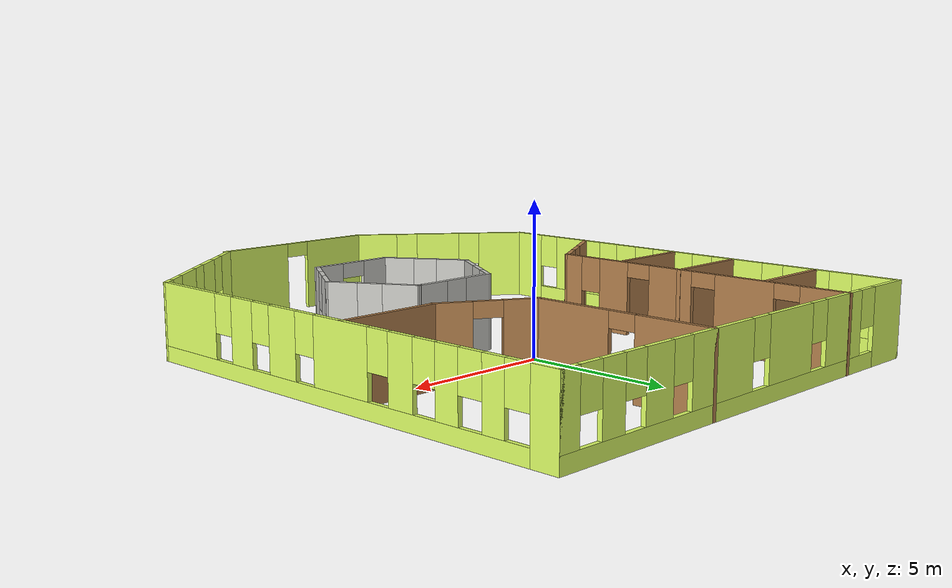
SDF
<?xml version='1.0'?>
<sdf version='1.6'>
  <model name='myBuilding'>
    <pose frame=''>-0.015237 -2.0117 0 0 -0 0</pose>
    <link name='Wall_1'>
      <pose frame=''>-7.98476 2.0117 0 0 -0 1.5708</pose>
      <visual name='Wall_1_Visual_0'>
        <pose frame=''>-7.43035 0 1.25 0 -0 0</pose>
        <geometry>
          <box>
            <size>1.2893 0.15 2.5</size>
          </box>
        </geometry>
        <material>
          <script>
            <uri>file://media/materials/scripts/gazebo.material</uri>
            <name>Gazebo/Grey</name>
          </script>
          <ambient>0.870588 1 0.4 1</ambient>
        </material>
        <meta>
          <layer>0</layer>
        </meta>
      </visual>
      <collision name='Wall_1_Collision_0'>
        <geometry>
          <box>
            <size>1.2893 0.15 2.5</size>
          </box>
        </geometry>
        <pose frame=''>-7.43035 0 1.25 0 -0 0</pose>
      </collision>
      <visual name='Wall_1_Visual_1'>
        <pose frame=''>0.64465 0 0.25 0 -0 0</pose>
        <geometry>
          <box>
            <size>14.8607 0.15 0.5</size>
          </box>
        </geometry>
        <material>
          <script>
            <uri>file://media/materials/scripts/gazebo.material</uri>
            <name>Gazebo/Grey</name>
          </script>
          <ambient>0.870588 1 0.4 1</ambient>
        </material>
        <meta>
          <layer>0</layer>
        </meta>
      </visual>
      <collision name='Wall_1_Collision_1'>
        <geometry>
          <box>
            <size>14.8607 0.15 0.5</size>
          </box>
        </geometry>
        <pose frame=''>0.64465 0 0.25 0 -0 0</pose>
      </collision>
      <visual name='Wall_1_Visual_2'>
        <pose frame=''>-4.91735 0 1.5 0 -0 0</pose>
        <geometry>
          <box>
            <size>2.13671 0.15 2</size>
          </box>
        </geometry>
        <material>
          <script>
            <uri>file://media/materials/scripts/gazebo.material</uri>
            <name>Gazebo/Grey</name>
          </script>
          <ambient>0.870588 1 0.4 1</ambient>
        </material>
        <meta>
          <layer>0</layer>
        </meta>
      </visual>
      <collision name='Wall_1_Collision_2'>
        <geometry>
          <box>
            <size>2.13671 0.15 2</size>
          </box>
        </geometry>
        <pose frame=''>-4.91735 0 1.5 0 -0 0</pose>
      </collision>
      <visual name='Wall_1_Visual_3'>
        <pose frame=''>-2.61971 0 1.5 0 -0 0</pose>
        <geometry>
          <box>
            <size>0.858577 0.15 2</size>
          </box>
        </geometry>
        <material>
          <script>
            <uri>file://media/materials/scripts/gazebo.material</uri>
            <name>Gazebo/Grey</name>
          </script>
          <ambient>0.870588 1 0.4 1</ambient>
        </material>
        <meta>
          <layer>0</layer>
        </meta>
      </visual>
      <collision name='Wall_1_Collision_3'>
        <geometry>
          <box>
            <size>0.858577 0.15 2</size>
          </box>
        </geometry>
        <pose frame=''>-2.61971 0 1.5 0 -0 0</pose>
      </collision>
      <visual name='Wall_1_Visual_4'>
        <pose frame=''>-0.533107 0 1.5 0 -0 0</pose>
        <geometry>
          <box>
            <size>1.71462 0.15 2</size>
          </box>
        </geometry>
        <material>
          <script>
            <uri>file://media/materials/scripts/gazebo.material</uri>
            <name>Gazebo/Grey</name>
          </script>
          <ambient>0.870588 1 0.4 1</ambient>
        </material>
        <meta>
          <layer>0</layer>
        </meta>
      </visual>
      <collision name='Wall_1_Collision_4'>
        <geometry>
          <box>
            <size>1.71462 0.15 2</size>
          </box>
        </geometry>
        <pose frame=''>-0.533107 0 1.5 0 -0 0</pose>
      </collision>
      <visual name='Wall_1_Visual_5'>
        <pose frame=''>2.14202 0 1.5 0 -0 0</pose>
        <geometry>
          <box>
            <size>2.03563 0.15 2</size>
          </box>
        </geometry>
        <material>
          <script>
            <uri>file://media/materials/scripts/gazebo.material</uri>
            <name>Gazebo/Grey</name>
          </script>
          <ambient>0.870588 1 0.4 1</ambient>
        </material>
        <meta>
          <layer>0</layer>
        </meta>
      </visual>
      <collision name='Wall_1_Collision_5'>
        <geometry>
          <box>
            <size>2.03563 0.15 2</size>
          </box>
        </geometry>
        <pose frame=''>2.14202 0 1.5 0 -0 0</pose>
      </collision>
      <visual name='Wall_1_Visual_6'>
        <pose frame=''>4.81656 0 1.5 0 -0 0</pose>
        <geometry>
          <box>
            <size>1.71345 0.15 2</size>
          </box>
        </geometry>
        <material>
          <script>
            <uri>file://media/materials/scripts/gazebo.material</uri>
            <name>Gazebo/Grey</name>
          </script>
          <ambient>0.870588 1 0.4 1</ambient>
        </material>
        <meta>
          <layer>0</layer>
        </meta>
      </visual>
      <collision name='Wall_1_Collision_6'>
        <geometry>
          <box>
            <size>1.71345 0.15 2</size>
          </box>
        </geometry>
        <pose frame=''>4.81656 0 1.5 0 -0 0</pose>
      </collision>
      <visual name='Wall_1_Visual_7'>
        <pose frame=''>7.27414 0 1.5 0 -0 0</pose>
        <geometry>
          <box>
            <size>1.60171 0.15 2</size>
          </box>
        </geometry>
        <material>
          <script>
            <uri>file://media/materials/scripts/gazebo.material</uri>
            <name>Gazebo/Grey</name>
          </script>
          <ambient>0.870588 1 0.4 1</ambient>
        </material>
        <meta>
          <layer>0</layer>
        </meta>
      </visual>
      <collision name='Wall_1_Collision_7'>
        <geometry>
          <box>
            <size>1.60171 0.15 2</size>
          </box>
        </geometry>
        <pose frame=''>7.27414 0 1.5 0 -0 0</pose>
      </collision>
      <visual name='Wall_1_Visual_8'>
        <pose frame=''>-6.3857 0 1.9 0 -0 0</pose>
        <geometry>
          <box>
            <size>0.8 0.15 1.2</size>
          </box>
        </geometry>
        <material>
          <script>
            <uri>file://media/materials/scripts/gazebo.material</uri>
            <name>Gazebo/Grey</name>
          </script>
          <ambient>0.870588 1 0.4 1</ambient>
        </material>
        <meta>
          <layer>0</layer>
        </meta>
      </visual>
      <collision name='Wall_1_Collision_8'>
        <geometry>
          <box>
            <size>0.8 0.15 1.2</size>
          </box>
        </geometry>
        <pose frame=''>-6.3857 0 1.9 0 -0 0</pose>
      </collision>
      <visual name='Wall_1_Visual_9'>
        <pose frame=''>-3.44899 0 1.9 0 -0 0</pose>
        <geometry>
          <box>
            <size>0.8 0.15 1.2</size>
          </box>
        </geometry>
        <material>
          <script>
            <uri>file://media/materials/scripts/gazebo.material</uri>
            <name>Gazebo/Grey</name>
          </script>
          <ambient>0.870588 1 0.4 1</ambient>
        </material>
        <meta>
          <layer>0</layer>
        </meta>
      </visual>
      <collision name='Wall_1_Collision_9'>
        <geometry>
          <box>
            <size>0.8 0.15 1.2</size>
          </box>
        </geometry>
        <pose frame=''>-3.44899 0 1.9 0 -0 0</pose>
      </collision>
      <visual name='Wall_1_Visual_10'>
        <pose frame=''>-1.79042 0 1.9 0 -0 0</pose>
        <geometry>
          <box>
            <size>0.8 0.15 1.2</size>
          </box>
        </geometry>
        <material>
          <script>
            <uri>file://media/materials/scripts/gazebo.material</uri>
            <name>Gazebo/Grey</name>
          </script>
          <ambient>0.870588 1 0.4 1</ambient>
        </material>
        <meta>
          <layer>0</layer>
        </meta>
      </visual>
      <collision name='Wall_1_Collision_10'>
        <geometry>
          <box>
            <size>0.8 0.15 1.2</size>
          </box>
        </geometry>
        <pose frame=''>-1.79042 0 1.9 0 -0 0</pose>
      </collision>
      <visual name='Wall_1_Visual_11'>
        <pose frame=''>0.724202 0 1.9 0 -0 0</pose>
        <geometry>
          <box>
            <size>0.8 0.15 1.2</size>
          </box>
        </geometry>
        <material>
          <script>
            <uri>file://media/materials/scripts/gazebo.material</uri>
            <name>Gazebo/Grey</name>
          </script>
          <ambient>0.870588 1 0.4 1</ambient>
        </material>
        <meta>
          <layer>0</layer>
        </meta>
      </visual>
      <collision name='Wall_1_Collision_11'>
        <geometry>
          <box>
            <size>0.8 0.15 1.2</size>
          </box>
        </geometry>
        <pose frame=''>0.724202 0 1.9 0 -0 0</pose>
      </collision>
      <visual name='Wall_1_Visual_12'>
        <pose frame=''>3.55983 0 1.9 0 -0 0</pose>
        <geometry>
          <box>
            <size>0.8 0.15 1.2</size>
          </box>
        </geometry>
        <material>
          <script>
            <uri>file://media/materials/scripts/gazebo.material</uri>
            <name>Gazebo/Grey</name>
          </script>
          <ambient>0.870588 1 0.4 1</ambient>
        </material>
        <meta>
          <layer>0</layer>
        </meta>
      </visual>
      <collision name='Wall_1_Collision_12'>
        <geometry>
          <box>
            <size>0.8 0.15 1.2</size>
          </box>
        </geometry>
        <pose frame=''>3.55983 0 1.9 0 -0 0</pose>
      </collision>
      <visual name='Wall_1_Visual_13'>
        <pose frame=''>6.07329 0 1.9 0 -0 0</pose>
        <geometry>
          <box>
            <size>0.8 0.15 1.2</size>
          </box>
        </geometry>
        <material>
          <script>
            <uri>file://media/materials/scripts/gazebo.material</uri>
            <name>Gazebo/Grey</name>
          </script>
          <ambient>0.870588 1 0.4 1</ambient>
        </material>
        <meta>
          <layer>0</layer>
        </meta>
      </visual>
      <collision name='Wall_1_Collision_13'>
        <geometry>
          <box>
            <size>0.8 0.15 1.2</size>
          </box>
        </geometry>
        <pose frame=''>6.07329 0 1.9 0 -0 0</pose>
      </collision>
    </link>
    <link name='Wall_10'>
      <pose frame=''>5.51524 -7.9883 0 0 0 -2.46685</pose>
      <visual name='Wall_10_Visual_0'>
        <pose frame=''>-3.02719 0 1.25 0 -0 0</pose>
        <geometry>
          <box>
            <size>0.498745 0.15 2.5</size>
          </box>
        </geometry>
        <material>
          <script>
            <uri>file://media/materials/scripts/gazebo.material</uri>
            <name>Gazebo/Grey</name>
          </script>
          <ambient>0.870588 1 0.4 1</ambient>
        </material>
        <meta>
          <layer>0</layer>
        </meta>
      </visual>
      <collision name='Wall_10_Collision_0'>
        <geometry>
          <box>
            <size>0.498745 0.15 2.5</size>
          </box>
        </geometry>
        <pose frame=''>-3.02719 0 1.25 0 -0 0</pose>
      </collision>
      <visual name='Wall_10_Visual_1'>
        <pose frame=''>0.249372 0 0.25 0 -0 0</pose>
        <geometry>
          <box>
            <size>6.05438 0.15 0.5</size>
          </box>
        </geometry>
        <material>
          <script>
            <uri>file://media/materials/scripts/gazebo.material</uri>
            <name>Gazebo/Grey</name>
          </script>
          <ambient>0.870588 1 0.4 1</ambient>
        </material>
        <meta>
          <layer>0</layer>
        </meta>
      </visual>
      <collision name='Wall_10_Collision_1'>
        <geometry>
          <box>
            <size>6.05438 0.15 0.5</size>
          </box>
        </geometry>
        <pose frame=''>0.249372 0 0.25 0 -0 0</pose>
      </collision>
      <visual name='Wall_10_Visual_2'>
        <pose frame=''>-1.31246 0 1.5 0 -0 0</pose>
        <geometry>
          <box>
            <size>1.33072 0.15 2</size>
          </box>
        </geometry>
        <material>
          <script>
            <uri>file://media/materials/scripts/gazebo.material</uri>
            <name>Gazebo/Grey</name>
          </script>
          <ambient>0.870588 1 0.4 1</ambient>
        </material>
        <meta>
          <layer>0</layer>
        </meta>
      </visual>
      <collision name='Wall_10_Collision_2'>
        <geometry>
          <box>
            <size>1.33072 0.15 2</size>
          </box>
        </geometry>
        <pose frame=''>-1.31246 0 1.5 0 -0 0</pose>
      </collision>
      <visual name='Wall_10_Visual_3'>
        <pose frame=''>0.732264 0 1.5 0 -0 0</pose>
        <geometry>
          <box>
            <size>1.15873 0.15 2</size>
          </box>
        </geometry>
        <material>
          <script>
            <uri>file://media/materials/scripts/gazebo.material</uri>
            <name>Gazebo/Grey</name>
          </script>
          <ambient>0.870588 1 0.4 1</ambient>
        </material>
        <meta>
          <layer>0</layer>
        </meta>
      </visual>
      <collision name='Wall_10_Collision_3'>
        <geometry>
          <box>
            <size>1.15873 0.15 2</size>
          </box>
        </geometry>
        <pose frame=''>0.732264 0 1.5 0 -0 0</pose>
      </collision>
      <visual name='Wall_10_Visual_4'>
        <pose frame=''>2.6941 0 1.5 0 -0 0</pose>
        <geometry>
          <box>
            <size>1.16493 0.15 2</size>
          </box>
        </geometry>
        <material>
          <script>
            <uri>file://media/materials/scripts/gazebo.material</uri>
            <name>Gazebo/Grey</name>
          </script>
          <ambient>0.870588 1 0.4 1</ambient>
        </material>
        <meta>
          <layer>0</layer>
        </meta>
      </visual>
      <collision name='Wall_10_Collision_4'>
        <geometry>
          <box>
            <size>1.16493 0.15 2</size>
          </box>
        </geometry>
        <pose frame=''>2.6941 0 1.5 0 -0 0</pose>
      </collision>
      <visual name='Wall_10_Visual_5'>
        <pose frame=''>-2.37782 0 1.9 0 -0 0</pose>
        <geometry>
          <box>
            <size>0.8 0.15 1.2</size>
          </box>
        </geometry>
        <material>
          <script>
            <uri>file://media/materials/scripts/gazebo.material</uri>
            <name>Gazebo/Grey</name>
          </script>
          <ambient>0.870588 1 0.4 1</ambient>
        </material>
        <meta>
          <layer>0</layer>
        </meta>
      </visual>
      <collision name='Wall_10_Collision_5'>
        <geometry>
          <box>
            <size>0.8 0.15 1.2</size>
          </box>
        </geometry>
        <pose frame=''>-2.37782 0 1.9 0 -0 0</pose>
      </collision>
      <visual name='Wall_10_Visual_6'>
        <pose frame=''>-0.247101 0 1.9 0 -0 0</pose>
        <geometry>
          <box>
            <size>0.8 0.15 1.2</size>
          </box>
        </geometry>
        <material>
          <script>
            <uri>file://media/materials/scripts/gazebo.material</uri>
            <name>Gazebo/Grey</name>
          </script>
          <ambient>0.870588 1 0.4 1</ambient>
        </material>
        <meta>
          <layer>0</layer>
        </meta>
      </visual>
      <collision name='Wall_10_Collision_6'>
        <geometry>
          <box>
            <size>0.8 0.15 1.2</size>
          </box>
        </geometry>
        <pose frame=''>-0.247101 0 1.9 0 -0 0</pose>
      </collision>
      <visual name='Wall_10_Visual_7'>
        <pose frame=''>1.71163 0 1.9 0 -0 0</pose>
        <geometry>
          <box>
            <size>0.8 0.15 1.2</size>
          </box>
        </geometry>
        <material>
          <script>
            <uri>file://media/materials/scripts/gazebo.material</uri>
            <name>Gazebo/Grey</name>
          </script>
          <ambient>0.870588 1 0.4 1</ambient>
        </material>
        <meta>
          <layer>0</layer>
        </meta>
      </visual>
      <collision name='Wall_10_Collision_7'>
        <geometry>
          <box>
            <size>0.8 0.15 1.2</size>
          </box>
        </geometry>
        <pose frame=''>1.71163 0 1.9 0 -0 0</pose>
      </collision>
    </link>
    <link name='Wall_12'>
      <pose frame=''>0.065237 -9.9883 0 0 -0 0</pose>
      <visual name='Wall_12_Visual_0'>
        <pose frame=''>-1.8125 0 1.25 0 -0 0</pose>
        <geometry>
          <box>
            <size>2.625 0.15 2.5</size>
          </box>
        </geometry>
        <material>
          <script>
            <uri>file://media/materials/scripts/gazebo.material</uri>
            <name>Gazebo/Grey</name>
          </script>
          <ambient>0.870588 1 0.4 1</ambient>
        </material>
        <meta>
          <layer>0</layer>
        </meta>
      </visual>
      <collision name='Wall_12_Collision_0'>
        <geometry>
          <box>
            <size>2.625 0.15 2.5</size>
          </box>
        </geometry>
        <pose frame=''>-1.8125 0 1.25 0 -0 0</pose>
      </collision>
      <visual name='Wall_12_Visual_1'>
        <pose frame=''>1.7625 0 1.25 0 -0 0</pose>
        <geometry>
          <box>
            <size>2.725 0.15 2.5</size>
          </box>
        </geometry>
        <material>
          <script>
            <uri>file://media/materials/scripts/gazebo.material</uri>
            <name>Gazebo/Grey</name>
          </script>
          <ambient>0.870588 1 0.4 1</ambient>
        </material>
        <meta>
          <layer>0</layer>
        </meta>
      </visual>
      <collision name='Wall_12_Collision_1'>
        <geometry>
          <box>
            <size>2.725 0.15 2.5</size>
          </box>
        </geometry>
        <pose frame=''>1.7625 0 1.25 0 -0 0</pose>
      </collision>
      <visual name='Wall_12_Visual_2'>
        <pose frame=''>-0.05 0 2.25 0 -0 0</pose>
        <geometry>
          <box>
            <size>0.9 0.15 0.5</size>
          </box>
        </geometry>
        <material>
          <script>
            <uri>file://media/materials/scripts/gazebo.material</uri>
            <name>Gazebo/Grey</name>
          </script>
          <ambient>0.870588 1 0.4 1</ambient>
        </material>
        <meta>
          <layer>0</layer>
        </meta>
      </visual>
      <collision name='Wall_12_Collision_2'>
        <geometry>
          <box>
            <size>0.9 0.15 0.5</size>
          </box>
        </geometry>
        <pose frame=''>-0.05 0 2.25 0 -0 0</pose>
      </collision>
    </link>
    <link name='Wall_14'>
      <pose frame=''>2.01524 7.0117 0 0 0 -1.5708</pose>
      <visual name='Wall_14_Visual_0'>
        <pose frame=''>-1.79003 0 1.25 0 -0 0</pose>
        <geometry>
          <box>
            <size>2.56994 0.15 2.5</size>
          </box>
        </geometry>
        <material>
          <script>
            <uri>file://media/materials/scripts/gazebo.material</uri>
            <name>Gazebo/Wood</name>
          </script>
          <ambient>1 0.976471 0.866667 1</ambient>
        </material>
        <meta>
          <layer>0</layer>
        </meta>
      </visual>
      <collision name='Wall_14_Collision_0'>
        <geometry>
          <box>
            <size>2.56994 0.15 2.5</size>
          </box>
        </geometry>
        <pose frame=''>-1.79003 0 1.25 0 -0 0</pose>
      </collision>
      <visual name='Wall_14_Visual_1'>
        <pose frame=''>1.73497 0 1.25 0 -0 0</pose>
        <geometry>
          <box>
            <size>2.68006 0.15 2.5</size>
          </box>
        </geometry>
        <material>
          <script>
            <uri>file://media/materials/scripts/gazebo.material</uri>
            <name>Gazebo/Wood</name>
          </script>
          <ambient>1 0.976471 0.866667 1</ambient>
        </material>
        <meta>
          <layer>0</layer>
        </meta>
      </visual>
      <collision name='Wall_14_Collision_1'>
        <geometry>
          <box>
            <size>2.68006 0.15 2.5</size>
          </box>
        </geometry>
        <pose frame=''>1.73497 0 1.25 0 -0 0</pose>
      </collision>
      <visual name='Wall_14_Visual_2'>
        <pose frame=''>-0.055061 0 2.25 0 -0 0</pose>
        <geometry>
          <box>
            <size>0.9 0.15 0.5</size>
          </box>
        </geometry>
        <material>
          <script>
            <uri>file://media/materials/scripts/gazebo.material</uri>
            <name>Gazebo/Wood</name>
          </script>
          <ambient>1 0.976471 0.866667 1</ambient>
        </material>
        <meta>
          <layer>0</layer>
        </meta>
      </visual>
      <collision name='Wall_14_Collision_2'>
        <geometry>
          <box>
            <size>0.9 0.15 0.5</size>
          </box>
        </geometry>
        <pose frame=''>-0.055061 0 2.25 0 -0 0</pose>
      </collision>
    </link>
    <link name='Wall_16'>
      <pose frame=''>3.35774 3.2367 0 0 0 -0.523547</pose>
      <visual name='Wall_16_Visual_0'>
        <pose frame=''>-1.0429 0 1.25 0 -0 0</pose>
        <geometry>
          <box>
            <size>1.1642 0.15 2.5</size>
          </box>
        </geometry>
        <material>
          <script>
            <uri>file://media/materials/scripts/gazebo.material</uri>
            <name>Gazebo/Wood</name>
          </script>
          <ambient>1 0.976471 0.866667 1</ambient>
        </material>
        <meta>
          <layer>0</layer>
        </meta>
      </visual>
      <collision name='Wall_16_Collision_0'>
        <geometry>
          <box>
            <size>1.1642 0.15 2.5</size>
          </box>
        </geometry>
        <pose frame=''>-1.0429 0 1.25 0 -0 0</pose>
      </collision>
      <visual name='Wall_16_Visual_1'>
        <pose frame=''>1.0321 0 1.25 0 -0 0</pose>
        <geometry>
          <box>
            <size>1.1858 0.15 2.5</size>
          </box>
        </geometry>
        <material>
          <script>
            <uri>file://media/materials/scripts/gazebo.material</uri>
            <name>Gazebo/Wood</name>
          </script>
          <ambient>1 0.976471 0.866667 1</ambient>
        </material>
        <meta>
          <layer>0</layer>
        </meta>
      </visual>
      <collision name='Wall_16_Collision_1'>
        <geometry>
          <box>
            <size>1.1858 0.15 2.5</size>
          </box>
        </geometry>
        <pose frame=''>1.0321 0 1.25 0 -0 0</pose>
      </collision>
      <visual name='Wall_16_Visual_2'>
        <pose frame=''>-0.010799 0 2.25 0 -0 0</pose>
        <geometry>
          <box>
            <size>0.9 0.15 0.5</size>
          </box>
        </geometry>
        <material>
          <script>
            <uri>file://media/materials/scripts/gazebo.material</uri>
            <name>Gazebo/Wood</name>
          </script>
          <ambient>1 0.976471 0.866667 1</ambient>
        </material>
        <meta>
          <layer>0</layer>
        </meta>
      </visual>
      <collision name='Wall_16_Collision_2'>
        <geometry>
          <box>
            <size>0.9 0.15 0.5</size>
          </box>
        </geometry>
        <pose frame=''>-0.010799 0 2.25 0 -0 0</pose>
      </collision>
    </link>
    <link name='Wall_18'>
      <collision name='Wall_18_Collision'>
        <geometry>
          <box>
            <size>3.465 0.15 2.5</size>
          </box>
        </geometry>
        <pose frame=''>0 0 1.25 0 -0 0</pose>
      </collision>
      <visual name='Wall_18_Visual'>
        <pose frame=''>0 0 1.25 0 -0 0</pose>
        <geometry>
          <box>
            <size>3.465 0.15 2.5</size>
          </box>
        </geometry>
        <material>
          <script>
            <uri>file://media/materials/scripts/gazebo.material</uri>
            <name>Gazebo/Wood</name>
          </script>
          <ambient>1 0.976471 0.866667 1</ambient>
        </material>
        <meta>
          <layer>0</layer>
        </meta>
      </visual>
      <pose frame=''>6.35774 2.4617 0 0 -0 0</pose>
    </link>
    <link name='Wall_21'>
      <pose frame=''>-4.90051 4.59371 0 0 0 -1.5708</pose>
      <visual name='Wall_21_Visual_0'>
        <pose frame=''>-4.67112 0 1.25 0 -0 0</pose>
        <geometry>
          <box>
            <size>1.65776 0.15 2.5</size>
          </box>
        </geometry>
        <material>
          <script>
            <uri>file://media/materials/scripts/gazebo.material</uri>
            <name>Gazebo/Wood</name>
          </script>
          <ambient>1 0.976471 0.866667 1</ambient>
        </material>
        <meta>
          <layer>0</layer>
        </meta>
      </visual>
      <collision name='Wall_21_Collision_0'>
        <geometry>
          <box>
            <size>1.65776 0.15 2.5</size>
          </box>
        </geometry>
        <pose frame=''>-4.67112 0 1.25 0 -0 0</pose>
      </collision>
      <visual name='Wall_21_Visual_1'>
        <pose frame=''>-1.86272 0 1.25 0 -0 0</pose>
        <geometry>
          <box>
            <size>2.15902 0.15 2.5</size>
          </box>
        </geometry>
        <material>
          <script>
            <uri>file://media/materials/scripts/gazebo.material</uri>
            <name>Gazebo/Wood</name>
          </script>
          <ambient>1 0.976471 0.866667 1</ambient>
        </material>
        <meta>
          <layer>0</layer>
        </meta>
      </visual>
      <collision name='Wall_21_Collision_1'>
        <geometry>
          <box>
            <size>2.15902 0.15 2.5</size>
          </box>
        </geometry>
        <pose frame=''>-1.86272 0 1.25 0 -0 0</pose>
      </collision>
      <visual name='Wall_21_Visual_2'>
        <pose frame=''>0.966873 0 1.25 0 -0 0</pose>
        <geometry>
          <box>
            <size>1.70017 0.15 2.5</size>
          </box>
        </geometry>
        <material>
          <script>
            <uri>file://media/materials/scripts/gazebo.material</uri>
            <name>Gazebo/Wood</name>
          </script>
          <ambient>1 0.976471 0.866667 1</ambient>
        </material>
        <meta>
          <layer>0</layer>
        </meta>
      </visual>
      <collision name='Wall_21_Collision_2'>
        <geometry>
          <box>
            <size>1.70017 0.15 2.5</size>
          </box>
        </geometry>
        <pose frame=''>0.966873 0 1.25 0 -0 0</pose>
      </collision>
      <visual name='Wall_21_Visual_3'>
        <pose frame=''>3.31748 0 1.25 0 -0 0</pose>
        <geometry>
          <box>
            <size>1.20104 0.15 2.5</size>
          </box>
        </geometry>
        <material>
          <script>
            <uri>file://media/materials/scripts/gazebo.material</uri>
            <name>Gazebo/Wood</name>
          </script>
          <ambient>1 0.976471 0.866667 1</ambient>
        </material>
        <meta>
          <layer>0</layer>
        </meta>
      </visual>
      <collision name='Wall_21_Collision_3'>
        <geometry>
          <box>
            <size>1.20104 0.15 2.5</size>
          </box>
        </geometry>
        <pose frame=''>3.31748 0 1.25 0 -0 0</pose>
      </collision>
      <visual name='Wall_21_Visual_4'>
        <pose frame=''>4.709 0 0.25 0 -0 0</pose>
        <geometry>
          <box>
            <size>1.582 0.15 0.5</size>
          </box>
        </geometry>
        <material>
          <script>
            <uri>file://media/materials/scripts/gazebo.material</uri>
            <name>Gazebo/Wood</name>
          </script>
          <ambient>1 0.976471 0.866667 1</ambient>
        </material>
        <meta>
          <layer>0</layer>
        </meta>
      </visual>
      <collision name='Wall_21_Collision_4'>
        <geometry>
          <box>
            <size>1.582 0.15 0.5</size>
          </box>
        </geometry>
        <pose frame=''>4.709 0 0.25 0 -0 0</pose>
      </collision>
      <visual name='Wall_21_Visual_5'>
        <pose frame=''>5.109 0 1.5 0 -0 0</pose>
        <geometry>
          <box>
            <size>0.782004 0.15 2</size>
          </box>
        </geometry>
        <material>
          <script>
            <uri>file://media/materials/scripts/gazebo.material</uri>
            <name>Gazebo/Wood</name>
          </script>
          <ambient>1 0.976471 0.866667 1</ambient>
        </material>
        <meta>
          <layer>0</layer>
        </meta>
      </visual>
      <collision name='Wall_21_Collision_5'>
        <geometry>
          <box>
            <size>0.782004 0.15 2</size>
          </box>
        </geometry>
        <pose frame=''>5.109 0 1.5 0 -0 0</pose>
      </collision>
      <visual name='Wall_21_Visual_6'>
        <pose frame=''>4.318 0 1.9 0 -0 0</pose>
        <geometry>
          <box>
            <size>0.8 0.15 1.2</size>
          </box>
        </geometry>
        <material>
          <script>
            <uri>file://media/materials/scripts/gazebo.material</uri>
            <name>Gazebo/Wood</name>
          </script>
          <ambient>1 0.976471 0.866667 1</ambient>
        </material>
        <meta>
          <layer>0</layer>
        </meta>
      </visual>
      <collision name='Wall_21_Collision_6'>
        <geometry>
          <box>
            <size>0.8 0.15 1.2</size>
          </box>
        </geometry>
        <pose frame=''>4.318 0 1.9 0 -0 0</pose>
      </collision>
      <visual name='Wall_21_Visual_7'>
        <pose frame=''>-3.39223 0 2.25 0 -0 0</pose>
        <geometry>
          <box>
            <size>0.9 0.15 0.5</size>
          </box>
        </geometry>
        <material>
          <script>
            <uri>file://media/materials/scripts/gazebo.material</uri>
            <name>Gazebo/Wood</name>
          </script>
          <ambient>1 0.976471 0.866667 1</ambient>
        </material>
        <meta>
          <layer>0</layer>
        </meta>
      </visual>
      <collision name='Wall_21_Collision_7'>
        <geometry>
          <box>
            <size>0.9 0.15 0.5</size>
          </box>
        </geometry>
        <pose frame=''>-3.39223 0 2.25 0 -0 0</pose>
      </collision>
      <visual name='Wall_21_Visual_8'>
        <pose frame=''>-0.333212 0 2.25 0 -0 0</pose>
        <geometry>
          <box>
            <size>0.9 0.15 0.5</size>
          </box>
        </geometry>
        <material>
          <script>
            <uri>file://media/materials/scripts/gazebo.material</uri>
            <name>Gazebo/Wood</name>
          </script>
          <ambient>1 0.976471 0.866667 1</ambient>
        </material>
        <meta>
          <layer>0</layer>
        </meta>
      </visual>
      <collision name='Wall_21_Collision_8'>
        <geometry>
          <box>
            <size>0.9 0.15 0.5</size>
          </box>
        </geometry>
        <pose frame=''>-0.333212 0 2.25 0 -0 0</pose>
      </collision>
      <visual name='Wall_21_Visual_9'>
        <pose frame=''>2.26696 0 2.25 0 -0 0</pose>
        <geometry>
          <box>
            <size>0.9 0.15 0.5</size>
          </box>
        </geometry>
        <material>
          <script>
            <uri>file://media/materials/scripts/gazebo.material</uri>
            <name>Gazebo/Wood</name>
          </script>
          <ambient>1 0.976471 0.866667 1</ambient>
        </material>
        <meta>
          <layer>0</layer>
        </meta>
      </visual>
      <collision name='Wall_21_Collision_9'>
        <geometry>
          <box>
            <size>0.9 0.15 0.5</size>
          </box>
        </geometry>
        <pose frame=''>2.26696 0 2.25 0 -0 0</pose>
      </collision>
    </link>
    <link name='Wall_22'>
      <pose frame=''>-6.45936 -1.73129 0 0 0 -2.61799</pose>
      <visual name='Wall_22_Visual_0'>
        <pose frame=''>-1.28514 0 1.25 0 -0 0</pose>
        <geometry>
          <box>
            <size>1.17972 0.15 2.5</size>
          </box>
        </geometry>
        <material>
          <script>
            <uri>file://media/materials/scripts/gazebo.material</uri>
            <name>Gazebo/Wood</name>
          </script>
          <ambient>1 0.976471 0.866667 1</ambient>
        </material>
        <meta>
          <layer>0</layer>
        </meta>
      </visual>
      <collision name='Wall_22_Collision_0'>
        <geometry>
          <box>
            <size>1.17972 0.15 2.5</size>
          </box>
        </geometry>
        <pose frame=''>-1.28514 0 1.25 0 -0 0</pose>
      </collision>
      <visual name='Wall_22_Visual_1'>
        <pose frame=''>1.03986 0 1.25 0 -0 0</pose>
        <geometry>
          <box>
            <size>1.67028 0.15 2.5</size>
          </box>
        </geometry>
        <material>
          <script>
            <uri>file://media/materials/scripts/gazebo.material</uri>
            <name>Gazebo/Wood</name>
          </script>
          <ambient>1 0.976471 0.866667 1</ambient>
        </material>
        <meta>
          <layer>0</layer>
        </meta>
      </visual>
      <collision name='Wall_22_Collision_1'>
        <geometry>
          <box>
            <size>1.67028 0.15 2.5</size>
          </box>
        </geometry>
        <pose frame=''>1.03986 0 1.25 0 -0 0</pose>
      </collision>
      <visual name='Wall_22_Visual_2'>
        <pose frame=''>-0.24528 0 2.25 0 -0 0</pose>
        <geometry>
          <box>
            <size>0.9 0.15 0.5</size>
          </box>
        </geometry>
        <material>
          <script>
            <uri>file://media/materials/scripts/gazebo.material</uri>
            <name>Gazebo/Wood</name>
          </script>
          <ambient>1 0.976471 0.866667 1</ambient>
        </material>
        <meta>
          <layer>0</layer>
        </meta>
      </visual>
      <collision name='Wall_22_Collision_2'>
        <geometry>
          <box>
            <size>0.9 0.15 0.5</size>
          </box>
        </geometry>
        <pose frame=''>-0.24528 0 2.25 0 -0 0</pose>
      </collision>
    </link>
    <link name='Wall_29'>
      <collision name='Wall_29_Collision'>
        <geometry>
          <box>
            <size>3.23933 0.15 2.5</size>
          </box>
        </geometry>
        <pose frame=''>0 0 1.25 0 -0 0</pose>
      </collision>
      <visual name='Wall_29_Visual'>
        <pose frame=''>0 0 1.25 0 -0 0</pose>
        <geometry>
          <box>
            <size>3.23933 0.15 2.5</size>
          </box>
        </geometry>
        <material>
          <script>
            <uri>file://media/materials/scripts/gazebo.material</uri>
            <name>Gazebo/Wood</name>
          </script>
          <ambient>1 0.976471 0.866667 1</ambient>
        </material>
        <meta>
          <layer>0</layer>
        </meta>
      </visual>
      <pose frame=''>-6.44026 3.9777 0 0 -0 0</pose>
    </link>
    <link name='Wall_31'>
      <collision name='Wall_31_Collision'>
        <geometry>
          <box>
            <size>3.234 0.15 2.5</size>
          </box>
        </geometry>
        <pose frame=''>0 0 1.25 0 -0 0</pose>
      </collision>
      <visual name='Wall_31_Visual'>
        <pose frame=''>0 0 1.25 0 -0 0</pose>
        <geometry>
          <box>
            <size>3.234 0.15 2.5</size>
          </box>
        </geometry>
        <material>
          <script>
            <uri>file://media/materials/scripts/gazebo.material</uri>
            <name>Gazebo/Wood</name>
          </script>
          <ambient>1 0.976471 0.866667 1</ambient>
        </material>
        <meta>
          <layer>0</layer>
        </meta>
      </visual>
      <pose frame=''>-6.44276 7.1467 0 0 -0 0</pose>
    </link>
    <link name='Wall_35'>
      <collision name='Wall_35_Collision'>
        <geometry>
          <box>
            <size>3.22684 0.15 2.5</size>
          </box>
        </geometry>
        <pose frame=''>0 0 1.25 0 -0 0</pose>
      </collision>
      <visual name='Wall_35_Visual'>
        <pose frame=''>0 0 1.25 0 -0 0</pose>
        <geometry>
          <box>
            <size>3.22684 0.15 2.5</size>
          </box>
        </geometry>
        <material>
          <script>
            <uri>file://media/materials/scripts/gazebo.material</uri>
            <name>Gazebo/Wood</name>
          </script>
          <ambient>1 0.976471 0.866667 1</ambient>
        </material>
        <meta>
          <layer>0</layer>
        </meta>
      </visual>
      <pose frame=''>-6.44626 1.5187 0 0 -0 0</pose>
    </link>
    <link name='Wall_37'>
      <pose frame=''>1.51524 0.011703 0 0 -0 0</pose>
      <visual name='Wall_37_Visual_0'>
        <pose frame=''>-1.00885 0 1.25 0 -0 0</pose>
        <geometry>
          <box>
            <size>1.1323 0.15 2.5</size>
          </box>
        </geometry>
        <material>
          <script>
            <uri>file://media/materials/scripts/gazebo.material</uri>
            <name>Gazebo/CeilingTiled</name>
          </script>
          <ambient>0.662745 0.929412 1 1</ambient>
        </material>
        <meta>
          <layer>0</layer>
        </meta>
      </visual>
      <collision name='Wall_37_Collision_0'>
        <geometry>
          <box>
            <size>1.1323 0.15 2.5</size>
          </box>
        </geometry>
        <pose frame=''>-1.00885 0 1.25 0 -0 0</pose>
      </collision>
      <visual name='Wall_37_Visual_1'>
        <pose frame=''>0.566152 0 0.25 0 -0 0</pose>
        <geometry>
          <box>
            <size>2.0177 0.15 0.5</size>
          </box>
        </geometry>
        <material>
          <script>
            <uri>file://media/materials/scripts/gazebo.material</uri>
            <name>Gazebo/CeilingTiled</name>
          </script>
          <ambient>0.662745 0.929412 1 1</ambient>
        </material>
        <meta>
          <layer>0</layer>
        </meta>
      </visual>
      <collision name='Wall_37_Collision_1'>
        <geometry>
          <box>
            <size>2.0177 0.15 0.5</size>
          </box>
        </geometry>
        <pose frame=''>0.566152 0 0.25 0 -0 0</pose>
      </collision>
      <visual name='Wall_37_Visual_2'>
        <pose frame=''>0.966152 0 1.5 0 -0 0</pose>
        <geometry>
          <box>
            <size>1.2177 0.15 2</size>
          </box>
        </geometry>
        <material>
          <script>
            <uri>file://media/materials/scripts/gazebo.material</uri>
            <name>Gazebo/CeilingTiled</name>
          </script>
          <ambient>0.662745 0.929412 1 1</ambient>
        </material>
        <meta>
          <layer>0</layer>
        </meta>
      </visual>
      <collision name='Wall_37_Collision_2'>
        <geometry>
          <box>
            <size>1.2177 0.15 2</size>
          </box>
        </geometry>
        <pose frame=''>0.966152 0 1.5 0 -0 0</pose>
      </collision>
      <visual name='Wall_37_Visual_3'>
        <pose frame=''>-0.042697 0 1.9 0 -0 0</pose>
        <geometry>
          <box>
            <size>0.8 0.15 1.2</size>
          </box>
        </geometry>
        <material>
          <script>
            <uri>file://media/materials/scripts/gazebo.material</uri>
            <name>Gazebo/CeilingTiled</name>
          </script>
          <ambient>0.662745 0.929412 1 1</ambient>
        </material>
        <meta>
          <layer>0</layer>
        </meta>
      </visual>
      <collision name='Wall_37_Collision_3'>
        <geometry>
          <box>
            <size>0.8 0.15 1.2</size>
          </box>
        </geometry>
        <pose frame=''>-0.042697 0 1.9 0 -0 0</pose>
      </collision>
    </link>
    <link name='Wall_4'>
      <pose frame=''>0.015237 10.0117 0 0 -0 0</pose>
      <visual name='Wall_4_Visual_0'>
        <pose frame=''>-7.22792 0 1.25 0 -0 0</pose>
        <geometry>
          <box>
            <size>1.69415 0.15 2.5</size>
          </box>
        </geometry>
        <material>
          <script>
            <uri>file://media/materials/scripts/gazebo.material</uri>
            <name>Gazebo/Grey</name>
          </script>
          <ambient>0.870588 1 0.4 1</ambient>
        </material>
        <meta>
          <layer>0</layer>
        </meta>
      </visual>
      <collision name='Wall_4_Collision_0'>
        <geometry>
          <box>
            <size>1.69415 0.15 2.5</size>
          </box>
        </geometry>
        <pose frame=''>-7.22792 0 1.25 0 -0 0</pose>
      </collision>
      <visual name='Wall_4_Visual_1'>
        <pose frame=''>0.847076 0 0.25 0 -0 0</pose>
        <geometry>
          <box>
            <size>14.4558 0.15 0.5</size>
          </box>
        </geometry>
        <material>
          <script>
            <uri>file://media/materials/scripts/gazebo.material</uri>
            <name>Gazebo/Grey</name>
          </script>
          <ambient>0.870588 1 0.4 1</ambient>
        </material>
        <meta>
          <layer>0</layer>
        </meta>
      </visual>
      <collision name='Wall_4_Collision_1'>
        <geometry>
          <box>
            <size>14.4558 0.15 0.5</size>
          </box>
        </geometry>
        <pose frame=''>0.847076 0 0.25 0 -0 0</pose>
      </collision>
      <visual name='Wall_4_Visual_2'>
        <pose frame=''>-4.58109 0 1.5 0 -0 0</pose>
        <geometry>
          <box>
            <size>1.99952 0.15 2</size>
          </box>
        </geometry>
        <material>
          <script>
            <uri>file://media/materials/scripts/gazebo.material</uri>
            <name>Gazebo/Grey</name>
          </script>
          <ambient>0.870588 1 0.4 1</ambient>
        </material>
        <meta>
          <layer>0</layer>
        </meta>
      </visual>
      <collision name='Wall_4_Collision_2'>
        <geometry>
          <box>
            <size>1.99952 0.15 2</size>
          </box>
        </geometry>
        <pose frame=''>-4.58109 0 1.5 0 -0 0</pose>
      </collision>
      <visual name='Wall_4_Visual_3'>
        <pose frame=''>-1.6739 0 1.5 0 -0 0</pose>
        <geometry>
          <box>
            <size>2.21487 0.15 2</size>
          </box>
        </geometry>
        <material>
          <script>
            <uri>file://media/materials/scripts/gazebo.material</uri>
            <name>Gazebo/Grey</name>
          </script>
          <ambient>0.870588 1 0.4 1</ambient>
        </material>
        <meta>
          <layer>0</layer>
        </meta>
      </visual>
      <collision name='Wall_4_Collision_3'>
        <geometry>
          <box>
            <size>2.21487 0.15 2</size>
          </box>
        </geometry>
        <pose frame=''>-1.6739 0 1.5 0 -0 0</pose>
      </collision>
      <visual name='Wall_4_Visual_4'>
        <pose frame=''>1.61784 0 1.5 0 -0 0</pose>
        <geometry>
          <box>
            <size>2.76862 0.15 2</size>
          </box>
        </geometry>
        <material>
          <script>
            <uri>file://media/materials/scripts/gazebo.material</uri>
            <name>Gazebo/Grey</name>
          </script>
          <ambient>0.870588 1 0.4 1</ambient>
        </material>
        <meta>
          <layer>0</layer>
        </meta>
      </visual>
      <collision name='Wall_4_Collision_4'>
        <geometry>
          <box>
            <size>2.76862 0.15 2</size>
          </box>
        </geometry>
        <pose frame=''>1.61784 0 1.5 0 -0 0</pose>
      </collision>
      <visual name='Wall_4_Visual_5'>
        <pose frame=''>4.35583 0 1.5 0 -0 0</pose>
        <geometry>
          <box>
            <size>1.10736 0.15 2</size>
          </box>
        </geometry>
        <material>
          <script>
            <uri>file://media/materials/scripts/gazebo.material</uri>
            <name>Gazebo/Grey</name>
          </script>
          <ambient>0.870588 1 0.4 1</ambient>
        </material>
        <meta>
          <layer>0</layer>
        </meta>
      </visual>
      <collision name='Wall_4_Collision_5'>
        <geometry>
          <box>
            <size>1.10736 0.15 2</size>
          </box>
        </geometry>
        <pose frame=''>4.35583 0 1.5 0 -0 0</pose>
      </collision>
      <visual name='Wall_4_Visual_6'>
        <pose frame=''>6.14014 0 1.5 0 -0 0</pose>
        <geometry>
          <box>
            <size>0.861253 0.15 2</size>
          </box>
        </geometry>
        <material>
          <script>
            <uri>file://media/materials/scripts/gazebo.material</uri>
            <name>Gazebo/Grey</name>
          </script>
          <ambient>0.870588 1 0.4 1</ambient>
        </material>
        <meta>
          <layer>0</layer>
        </meta>
      </visual>
      <collision name='Wall_4_Collision_6'>
        <geometry>
          <box>
            <size>0.861253 0.15 2</size>
          </box>
        </geometry>
        <pose frame=''>6.14014 0 1.5 0 -0 0</pose>
      </collision>
      <visual name='Wall_4_Visual_7'>
        <pose frame=''>7.72288 0 1.5 0 -0 0</pose>
        <geometry>
          <box>
            <size>0.704231 0.15 2</size>
          </box>
        </geometry>
        <material>
          <script>
            <uri>file://media/materials/scripts/gazebo.material</uri>
            <name>Gazebo/Grey</name>
          </script>
          <ambient>0.870588 1 0.4 1</ambient>
        </material>
        <meta>
          <layer>0</layer>
        </meta>
      </visual>
      <collision name='Wall_4_Collision_7'>
        <geometry>
          <box>
            <size>0.704231 0.15 2</size>
          </box>
        </geometry>
        <pose frame=''>7.72288 0 1.5 0 -0 0</pose>
      </collision>
      <visual name='Wall_4_Visual_8'>
        <pose frame=''>-5.98085 0 1.9 0 -0 0</pose>
        <geometry>
          <box>
            <size>0.8 0.15 1.2</size>
          </box>
        </geometry>
        <material>
          <script>
            <uri>file://media/materials/scripts/gazebo.material</uri>
            <name>Gazebo/Grey</name>
          </script>
          <ambient>0.870588 1 0.4 1</ambient>
        </material>
        <meta>
          <layer>0</layer>
        </meta>
      </visual>
      <collision name='Wall_4_Collision_8'>
        <geometry>
          <box>
            <size>0.8 0.15 1.2</size>
          </box>
        </geometry>
        <pose frame=''>-5.98085 0 1.9 0 -0 0</pose>
      </collision>
      <visual name='Wall_4_Visual_9'>
        <pose frame=''>-3.18133 0 1.9 0 -0 0</pose>
        <geometry>
          <box>
            <size>0.8 0.15 1.2</size>
          </box>
        </geometry>
        <material>
          <script>
            <uri>file://media/materials/scripts/gazebo.material</uri>
            <name>Gazebo/Grey</name>
          </script>
          <ambient>0.870588 1 0.4 1</ambient>
        </material>
        <meta>
          <layer>0</layer>
        </meta>
      </visual>
      <collision name='Wall_4_Collision_9'>
        <geometry>
          <box>
            <size>0.8 0.15 1.2</size>
          </box>
        </geometry>
        <pose frame=''>-3.18133 0 1.9 0 -0 0</pose>
      </collision>
      <visual name='Wall_4_Visual_10'>
        <pose frame=''>-0.166464 0 1.9 0 -0 0</pose>
        <geometry>
          <box>
            <size>0.8 0.15 1.2</size>
          </box>
        </geometry>
        <material>
          <script>
            <uri>file://media/materials/scripts/gazebo.material</uri>
            <name>Gazebo/Grey</name>
          </script>
          <ambient>0.870588 1 0.4 1</ambient>
        </material>
        <meta>
          <layer>0</layer>
        </meta>
      </visual>
      <collision name='Wall_4_Collision_10'>
        <geometry>
          <box>
            <size>0.8 0.15 1.2</size>
          </box>
        </geometry>
        <pose frame=''>-0.166464 0 1.9 0 -0 0</pose>
      </collision>
      <visual name='Wall_4_Visual_11'>
        <pose frame=''>3.40215 0 1.9 0 -0 0</pose>
        <geometry>
          <box>
            <size>0.8 0.15 1.2</size>
          </box>
        </geometry>
        <material>
          <script>
            <uri>file://media/materials/scripts/gazebo.material</uri>
            <name>Gazebo/Grey</name>
          </script>
          <ambient>0.870588 1 0.4 1</ambient>
        </material>
        <meta>
          <layer>0</layer>
        </meta>
      </visual>
      <collision name='Wall_4_Collision_11'>
        <geometry>
          <box>
            <size>0.8 0.15 1.2</size>
          </box>
        </geometry>
        <pose frame=''>3.40215 0 1.9 0 -0 0</pose>
      </collision>
      <visual name='Wall_4_Visual_12'>
        <pose frame=''>5.30952 0 1.9 0 -0 0</pose>
        <geometry>
          <box>
            <size>0.8 0.15 1.2</size>
          </box>
        </geometry>
        <material>
          <script>
            <uri>file://media/materials/scripts/gazebo.material</uri>
            <name>Gazebo/Grey</name>
          </script>
          <ambient>0.870588 1 0.4 1</ambient>
        </material>
        <meta>
          <layer>0</layer>
        </meta>
      </visual>
      <collision name='Wall_4_Collision_12'>
        <geometry>
          <box>
            <size>0.8 0.15 1.2</size>
          </box>
        </geometry>
        <pose frame=''>5.30952 0 1.9 0 -0 0</pose>
      </collision>
      <visual name='Wall_4_Visual_13'>
        <pose frame=''>6.97077 0 1.9 0 -0 0</pose>
        <geometry>
          <box>
            <size>0.8 0.15 1.2</size>
          </box>
        </geometry>
        <material>
          <script>
            <uri>file://media/materials/scripts/gazebo.material</uri>
            <name>Gazebo/Grey</name>
          </script>
          <ambient>0.870588 1 0.4 1</ambient>
        </material>
        <meta>
          <layer>0</layer>
        </meta>
      </visual>
      <collision name='Wall_4_Collision_13'>
        <geometry>
          <box>
            <size>0.8 0.15 1.2</size>
          </box>
        </geometry>
        <pose frame=''>6.97077 0 1.9 0 -0 0</pose>
      </collision>
    </link>
    <link name='Wall_41'>
      <pose frame=''>1.55274 -4.8883 0 0 -0 3.14159</pose>
      <visual name='Wall_41_Visual_0'>
        <pose frame=''>-0.993879 0 1.25 0 -0 0</pose>
        <geometry>
          <box>
            <size>1.08724 0.15 2.5</size>
          </box>
        </geometry>
        <material>
          <script>
            <uri>file://media/materials/scripts/gazebo.material</uri>
            <name>Gazebo/CeilingTiled</name>
          </script>
          <ambient>0.662745 0.929412 1 1</ambient>
        </material>
        <meta>
          <layer>0</layer>
        </meta>
      </visual>
      <collision name='Wall_41_Collision_0'>
        <geometry>
          <box>
            <size>1.08724 0.15 2.5</size>
          </box>
        </geometry>
        <pose frame=''>-0.993879 0 1.25 0 -0 0</pose>
      </collision>
      <visual name='Wall_41_Visual_1'>
        <pose frame=''>0.993621 0 1.25 0 -0 0</pose>
        <geometry>
          <box>
            <size>1.08776 0.15 2.5</size>
          </box>
        </geometry>
        <material>
          <script>
            <uri>file://media/materials/scripts/gazebo.material</uri>
            <name>Gazebo/CeilingTiled</name>
          </script>
          <ambient>0.662745 0.929412 1 1</ambient>
        </material>
        <meta>
          <layer>0</layer>
        </meta>
      </visual>
      <collision name='Wall_41_Collision_1'>
        <geometry>
          <box>
            <size>1.08776 0.15 2.5</size>
          </box>
        </geometry>
        <pose frame=''>0.993621 0 1.25 0 -0 0</pose>
      </collision>
      <visual name='Wall_41_Visual_2'>
        <pose frame=''>-0.000257 0 2.25 0 -0 0</pose>
        <geometry>
          <box>
            <size>0.9 0.15 0.5</size>
          </box>
        </geometry>
        <material>
          <script>
            <uri>file://media/materials/scripts/gazebo.material</uri>
            <name>Gazebo/CeilingTiled</name>
          </script>
          <ambient>0.662745 0.929412 1 1</ambient>
        </material>
        <meta>
          <layer>0</layer>
        </meta>
      </visual>
      <collision name='Wall_41_Collision_2'>
        <geometry>
          <box>
            <size>0.9 0.15 0.5</size>
          </box>
        </geometry>
        <pose frame=''>-0.000257 0 2.25 0 -0 0</pose>
      </collision>
    </link>
    <link name='Wall_46'>
      <pose frame=''>-0.734763 -1.2383 0 0 0 -2.11122</pose>
      <visual name='Wall_46_Visual_0'>
        <pose frame=''>-1.10227 0 1.25 0 -0 0</pose>
        <geometry>
          <box>
            <size>0.860943 0.15 2.5</size>
          </box>
        </geometry>
        <material>
          <script>
            <uri>file://media/materials/scripts/gazebo.material</uri>
            <name>Gazebo/CeilingTiled</name>
          </script>
          <ambient>0.662745 0.929412 1 1</ambient>
        </material>
        <meta>
          <layer>0</layer>
        </meta>
      </visual>
      <collision name='Wall_46_Collision_0'>
        <geometry>
          <box>
            <size>0.860943 0.15 2.5</size>
          </box>
        </geometry>
        <pose frame=''>-1.10227 0 1.25 0 -0 0</pose>
      </collision>
      <visual name='Wall_46_Visual_1'>
        <pose frame=''>0.880472 0 1.25 0 -0 0</pose>
        <geometry>
          <box>
            <size>1.30453 0.15 2.5</size>
          </box>
        </geometry>
        <material>
          <script>
            <uri>file://media/materials/scripts/gazebo.material</uri>
            <name>Gazebo/CeilingTiled</name>
          </script>
          <ambient>0.662745 0.929412 1 1</ambient>
        </material>
        <meta>
          <layer>0</layer>
        </meta>
      </visual>
      <collision name='Wall_46_Collision_1'>
        <geometry>
          <box>
            <size>1.30453 0.15 2.5</size>
          </box>
        </geometry>
        <pose frame=''>0.880472 0 1.25 0 -0 0</pose>
      </collision>
      <visual name='Wall_46_Visual_2'>
        <pose frame=''>-0.221794 0 2.25 0 -0 0</pose>
        <geometry>
          <box>
            <size>0.9 0.15 0.5</size>
          </box>
        </geometry>
        <material>
          <script>
            <uri>file://media/materials/scripts/gazebo.material</uri>
            <name>Gazebo/CeilingTiled</name>
          </script>
          <ambient>0.662745 0.929412 1 1</ambient>
        </material>
        <meta>
          <layer>0</layer>
        </meta>
      </visual>
      <collision name='Wall_46_Collision_2'>
        <geometry>
          <box>
            <size>0.9 0.15 0.5</size>
          </box>
        </geometry>
        <pose frame=''>-0.221794 0 2.25 0 -0 0</pose>
      </collision>
    </link>
    <link name='Wall_47'>
      <pose frame=''>-0.697263 -3.6883 0 0 0 -0.99004</pose>
      <visual name='Wall_47_Visual_0'>
        <pose frame=''>-0.962388 0 1.25 0 -0 0</pose>
        <geometry>
          <box>
            <size>1.09587 0.15 2.5</size>
          </box>
        </geometry>
        <material>
          <script>
            <uri>file://media/materials/scripts/gazebo.material</uri>
            <name>Gazebo/CeilingTiled</name>
          </script>
          <ambient>0.662745 0.929412 1 1</ambient>
        </material>
        <meta>
          <layer>0</layer>
        </meta>
      </visual>
      <collision name='Wall_47_Collision_0'>
        <geometry>
          <box>
            <size>1.09587 0.15 2.5</size>
          </box>
        </geometry>
        <pose frame=''>-0.962388 0 1.25 0 -0 0</pose>
      </collision>
      <visual name='Wall_47_Visual_1'>
        <pose frame=''>0.547936 0 0.25 0 -0 0</pose>
        <geometry>
          <box>
            <size>1.92478 0.15 0.5</size>
          </box>
        </geometry>
        <material>
          <script>
            <uri>file://media/materials/scripts/gazebo.material</uri>
            <name>Gazebo/CeilingTiled</name>
          </script>
          <ambient>0.662745 0.929412 1 1</ambient>
        </material>
        <meta>
          <layer>0</layer>
        </meta>
      </visual>
      <collision name='Wall_47_Collision_1'>
        <geometry>
          <box>
            <size>1.92478 0.15 0.5</size>
          </box>
        </geometry>
        <pose frame=''>0.547936 0 0.25 0 -0 0</pose>
      </collision>
      <visual name='Wall_47_Visual_2'>
        <pose frame=''>0.947936 0 1.5 0 -0 0</pose>
        <geometry>
          <box>
            <size>1.12478 0.15 2</size>
          </box>
        </geometry>
        <material>
          <script>
            <uri>file://media/materials/scripts/gazebo.material</uri>
            <name>Gazebo/CeilingTiled</name>
          </script>
          <ambient>0.662745 0.929412 1 1</ambient>
        </material>
        <meta>
          <layer>0</layer>
        </meta>
      </visual>
      <collision name='Wall_47_Collision_2'>
        <geometry>
          <box>
            <size>1.12478 0.15 2</size>
          </box>
        </geometry>
        <pose frame=''>0.947936 0 1.5 0 -0 0</pose>
      </collision>
      <visual name='Wall_47_Visual_3'>
        <pose frame=''>-0.014452 0 1.9 0 -0 0</pose>
        <geometry>
          <box>
            <size>0.8 0.15 1.2</size>
          </box>
        </geometry>
        <material>
          <script>
            <uri>file://media/materials/scripts/gazebo.material</uri>
            <name>Gazebo/CeilingTiled</name>
          </script>
          <ambient>0.662745 0.929412 1 1</ambient>
        </material>
        <meta>
          <layer>0</layer>
        </meta>
      </visual>
      <collision name='Wall_47_Collision_3'>
        <geometry>
          <box>
            <size>0.8 0.15 1.2</size>
          </box>
        </geometry>
        <pose frame=''>-0.014452 0 1.9 0 -0 0</pose>
      </collision>
    </link>
    <link name='Wall_49'>
      <pose frame=''>3.76524 -1.2383 0 0 0 -1.03038</pose>
      <visual name='Wall_49_Visual_0'>
        <pose frame=''>-0.922396 0 1.25 0 -0 0</pose>
        <geometry>
          <box>
            <size>1.22069 0.15 2.5</size>
          </box>
        </geometry>
        <material>
          <script>
            <uri>file://media/materials/scripts/gazebo.material</uri>
            <name>Gazebo/CeilingTiled</name>
          </script>
          <ambient>0.662745 0.929412 1 1</ambient>
        </material>
        <meta>
          <layer>0</layer>
        </meta>
      </visual>
      <collision name='Wall_49_Collision_0'>
        <geometry>
          <box>
            <size>1.22069 0.15 2.5</size>
          </box>
        </geometry>
        <pose frame=''>-0.922396 0 1.25 0 -0 0</pose>
      </collision>
      <visual name='Wall_49_Visual_1'>
        <pose frame=''>0.610342 0 0.25 0 -0 0</pose>
        <geometry>
          <box>
            <size>1.84479 0.15 0.5</size>
          </box>
        </geometry>
        <material>
          <script>
            <uri>file://media/materials/scripts/gazebo.material</uri>
            <name>Gazebo/CeilingTiled</name>
          </script>
          <ambient>0.662745 0.929412 1 1</ambient>
        </material>
        <meta>
          <layer>0</layer>
        </meta>
      </visual>
      <collision name='Wall_49_Collision_1'>
        <geometry>
          <box>
            <size>1.84479 0.15 0.5</size>
          </box>
        </geometry>
        <pose frame=''>0.610342 0 0.25 0 -0 0</pose>
      </collision>
      <visual name='Wall_49_Visual_2'>
        <pose frame=''>1.01034 0 1.5 0 -0 0</pose>
        <geometry>
          <box>
            <size>1.04479 0.15 2</size>
          </box>
        </geometry>
        <material>
          <script>
            <uri>file://media/materials/scripts/gazebo.material</uri>
            <name>Gazebo/CeilingTiled</name>
          </script>
          <ambient>0.662745 0.929412 1 1</ambient>
        </material>
        <meta>
          <layer>0</layer>
        </meta>
      </visual>
      <collision name='Wall_49_Collision_2'>
        <geometry>
          <box>
            <size>1.04479 0.15 2</size>
          </box>
        </geometry>
        <pose frame=''>1.01034 0 1.5 0 -0 0</pose>
      </collision>
      <visual name='Wall_49_Visual_3'>
        <pose frame=''>0.087947 0 1.9 0 -0 0</pose>
        <geometry>
          <box>
            <size>0.8 0.15 1.2</size>
          </box>
        </geometry>
        <material>
          <script>
            <uri>file://media/materials/scripts/gazebo.material</uri>
            <name>Gazebo/CeilingTiled</name>
          </script>
          <ambient>0.662745 0.929412 1 1</ambient>
        </material>
        <meta>
          <layer>0</layer>
        </meta>
      </visual>
      <collision name='Wall_49_Collision_3'>
        <geometry>
          <box>
            <size>0.8 0.15 1.2</size>
          </box>
        </geometry>
        <pose frame=''>0.087947 0 1.9 0 -0 0</pose>
      </collision>
    </link>
    <link name='Wall_50'>
      <pose frame=''>3.76524 -3.6883 0 0 0 -2.1294</pose>
      <visual name='Wall_50_Visual_0'>
        <pose frame=''>-0.889397 0 1.25 0 -0 0</pose>
        <geometry>
          <box>
            <size>1.2014 0.15 2.5</size>
          </box>
        </geometry>
        <material>
          <script>
            <uri>file://media/materials/scripts/gazebo.material</uri>
            <name>Gazebo/CeilingTiled</name>
          </script>
          <ambient>0.662745 0.929412 1 1</ambient>
        </material>
        <meta>
          <layer>0</layer>
        </meta>
      </visual>
      <collision name='Wall_50_Collision_0'>
        <geometry>
          <box>
            <size>1.2014 0.15 2.5</size>
          </box>
        </geometry>
        <pose frame=''>-0.889397 0 1.25 0 -0 0</pose>
      </collision>
      <visual name='Wall_50_Visual_1'>
        <pose frame=''>0.6007 0 0.25 0 -0 0</pose>
        <geometry>
          <box>
            <size>1.77879 0.15 0.5</size>
          </box>
        </geometry>
        <material>
          <script>
            <uri>file://media/materials/scripts/gazebo.material</uri>
            <name>Gazebo/CeilingTiled</name>
          </script>
          <ambient>0.662745 0.929412 1 1</ambient>
        </material>
        <meta>
          <layer>0</layer>
        </meta>
      </visual>
      <collision name='Wall_50_Collision_1'>
        <geometry>
          <box>
            <size>1.77879 0.15 0.5</size>
          </box>
        </geometry>
        <pose frame=''>0.6007 0 0.25 0 -0 0</pose>
      </collision>
      <visual name='Wall_50_Visual_2'>
        <pose frame=''>1.0007 0 1.5 0 -0 0</pose>
        <geometry>
          <box>
            <size>0.978794 0.15 2</size>
          </box>
        </geometry>
        <material>
          <script>
            <uri>file://media/materials/scripts/gazebo.material</uri>
            <name>Gazebo/CeilingTiled</name>
          </script>
          <ambient>0.662745 0.929412 1 1</ambient>
        </material>
        <meta>
          <layer>0</layer>
        </meta>
      </visual>
      <collision name='Wall_50_Collision_2'>
        <geometry>
          <box>
            <size>0.978794 0.15 2</size>
          </box>
        </geometry>
        <pose frame=''>1.0007 0 1.5 0 -0 0</pose>
      </collision>
      <visual name='Wall_50_Visual_3'>
        <pose frame=''>0.111303 0 1.9 0 -0 0</pose>
        <geometry>
          <box>
            <size>0.8 0.15 1.2</size>
          </box>
        </geometry>
        <material>
          <script>
            <uri>file://media/materials/scripts/gazebo.material</uri>
            <name>Gazebo/CeilingTiled</name>
          </script>
          <ambient>0.662745 0.929412 1 1</ambient>
        </material>
        <meta>
          <layer>0</layer>
        </meta>
      </visual>
      <collision name='Wall_50_Collision_3'>
        <geometry>
          <box>
            <size>0.8 0.15 1.2</size>
          </box>
        </geometry>
        <pose frame=''>0.111303 0 1.9 0 -0 0</pose>
      </collision>
    </link>
    <link name='Wall_6'>
      <pose frame=''>8.01524 2.0117 0 0 0 -1.5708</pose>
      <visual name='Wall_6_Visual_0'>
        <pose frame=''>-7.62793 0 1.25 0 -0 0</pose>
        <geometry>
          <box>
            <size>0.89414 0.15 2.5</size>
          </box>
        </geometry>
        <material>
          <script>
            <uri>file://media/materials/scripts/gazebo.material</uri>
            <name>Gazebo/Grey</name>
          </script>
          <ambient>0.870588 1 0.4 1</ambient>
        </material>
        <meta>
          <layer>0</layer>
        </meta>
      </visual>
      <collision name='Wall_6_Collision_0'>
        <geometry>
          <box>
            <size>0.89414 0.15 2.5</size>
          </box>
        </geometry>
        <pose frame=''>-7.62793 0 1.25 0 -0 0</pose>
      </collision>
      <visual name='Wall_6_Visual_1'>
        <pose frame=''>0.44707 0 0.25 0 -0 0</pose>
        <geometry>
          <box>
            <size>15.2559 0.15 0.5</size>
          </box>
        </geometry>
        <material>
          <script>
            <uri>file://media/materials/scripts/gazebo.material</uri>
            <name>Gazebo/Grey</name>
          </script>
          <ambient>0.870588 1 0.4 1</ambient>
        </material>
        <meta>
          <layer>0</layer>
        </meta>
      </visual>
      <collision name='Wall_6_Collision_1'>
        <geometry>
          <box>
            <size>15.2559 0.15 0.5</size>
          </box>
        </geometry>
        <pose frame=''>0.44707 0 0.25 0 -0 0</pose>
      </collision>
      <visual name='Wall_6_Visual_2'>
        <pose frame=''>-6.01176 0 1.5 0 -0 0</pose>
        <geometry>
          <box>
            <size>0.738197 0.15 2</size>
          </box>
        </geometry>
        <material>
          <script>
            <uri>file://media/materials/scripts/gazebo.material</uri>
            <name>Gazebo/Grey</name>
          </script>
          <ambient>0.870588 1 0.4 1</ambient>
        </material>
        <meta>
          <layer>0</layer>
        </meta>
      </visual>
      <collision name='Wall_6_Collision_2'>
        <geometry>
          <box>
            <size>0.738197 0.15 2</size>
          </box>
        </geometry>
        <pose frame=''>-6.01176 0 1.5 0 -0 0</pose>
      </collision>
      <visual name='Wall_6_Visual_3'>
        <pose frame=''>-4.4428 0 1.5 0 -0 0</pose>
        <geometry>
          <box>
            <size>0.799725 0.15 2</size>
          </box>
        </geometry>
        <material>
          <script>
            <uri>file://media/materials/scripts/gazebo.material</uri>
            <name>Gazebo/Grey</name>
          </script>
          <ambient>0.870588 1 0.4 1</ambient>
        </material>
        <meta>
          <layer>0</layer>
        </meta>
      </visual>
      <collision name='Wall_6_Collision_3'>
        <geometry>
          <box>
            <size>0.799725 0.15 2</size>
          </box>
        </geometry>
        <pose frame=''>-4.4428 0 1.5 0 -0 0</pose>
      </collision>
      <visual name='Wall_6_Visual_4'>
        <pose frame=''>-2.78155 0 1.5 0 -0 0</pose>
        <geometry>
          <box>
            <size>0.922781 0.15 2</size>
          </box>
        </geometry>
        <material>
          <script>
            <uri>file://media/materials/scripts/gazebo.material</uri>
            <name>Gazebo/Grey</name>
          </script>
          <ambient>0.870588 1 0.4 1</ambient>
        </material>
        <meta>
          <layer>0</layer>
        </meta>
      </visual>
      <collision name='Wall_6_Collision_4'>
        <geometry>
          <box>
            <size>0.922781 0.15 2</size>
          </box>
        </geometry>
        <pose frame=''>-2.78155 0 1.5 0 -0 0</pose>
      </collision>
      <visual name='Wall_6_Visual_5'>
        <pose frame=''>-0.412725 0 1.5 0 -0 0</pose>
        <geometry>
          <box>
            <size>2.21487 0.15 2</size>
          </box>
        </geometry>
        <material>
          <script>
            <uri>file://media/materials/scripts/gazebo.material</uri>
            <name>Gazebo/Grey</name>
          </script>
          <ambient>0.870588 1 0.4 1</ambient>
        </material>
        <meta>
          <layer>0</layer>
        </meta>
      </visual>
      <collision name='Wall_6_Collision_5'>
        <geometry>
          <box>
            <size>2.21487 0.15 2</size>
          </box>
        </geometry>
        <pose frame=''>-0.412725 0 1.5 0 -0 0</pose>
      </collision>
      <visual name='Wall_6_Visual_6'>
        <pose frame=''>2.09454 0 1.5 0 -0 0</pose>
        <geometry>
          <box>
            <size>1.19966 0.15 2</size>
          </box>
        </geometry>
        <material>
          <script>
            <uri>file://media/materials/scripts/gazebo.material</uri>
            <name>Gazebo/Grey</name>
          </script>
          <ambient>0.870588 1 0.4 1</ambient>
        </material>
        <meta>
          <layer>0</layer>
        </meta>
      </visual>
      <collision name='Wall_6_Collision_6'>
        <geometry>
          <box>
            <size>1.19966 0.15 2</size>
          </box>
        </geometry>
        <pose frame=''>2.09454 0 1.5 0 -0 0</pose>
      </collision>
      <visual name='Wall_6_Visual_7'>
        <pose frame=''>4.0019 0 1.5 0 -0 0</pose>
        <geometry>
          <box>
            <size>1.01507 0.15 2</size>
          </box>
        </geometry>
        <material>
          <script>
            <uri>file://media/materials/scripts/gazebo.material</uri>
            <name>Gazebo/Grey</name>
          </script>
          <ambient>0.870588 1 0.4 1</ambient>
        </material>
        <meta>
          <layer>0</layer>
        </meta>
      </visual>
      <collision name='Wall_6_Collision_7'>
        <geometry>
          <box>
            <size>1.01507 0.15 2</size>
          </box>
        </geometry>
        <pose frame=''>4.0019 0 1.5 0 -0 0</pose>
      </collision>
      <visual name='Wall_6_Visual_8'>
        <pose frame=''>6.69222 0 1.5 0 -0 0</pose>
        <geometry>
          <box>
            <size>2.76556 0.15 2</size>
          </box>
        </geometry>
        <material>
          <script>
            <uri>file://media/materials/scripts/gazebo.material</uri>
            <name>Gazebo/Grey</name>
          </script>
          <ambient>0.870588 1 0.4 1</ambient>
        </material>
        <meta>
          <layer>0</layer>
        </meta>
      </visual>
      <collision name='Wall_6_Collision_8'>
        <geometry>
          <box>
            <size>2.76556 0.15 2</size>
          </box>
        </geometry>
        <pose frame=''>6.69222 0 1.5 0 -0 0</pose>
      </collision>
      <visual name='Wall_6_Visual_9'>
        <pose frame=''>-6.78086 0 1.9 0 -0 0</pose>
        <geometry>
          <box>
            <size>0.8 0.15 1.2</size>
          </box>
        </geometry>
        <material>
          <script>
            <uri>file://media/materials/scripts/gazebo.material</uri>
            <name>Gazebo/Grey</name>
          </script>
          <ambient>0.870588 1 0.4 1</ambient>
        </material>
        <meta>
          <layer>0</layer>
        </meta>
      </visual>
      <collision name='Wall_6_Collision_9'>
        <geometry>
          <box>
            <size>0.8 0.15 1.2</size>
          </box>
        </geometry>
        <pose frame=''>-6.78086 0 1.9 0 -0 0</pose>
      </collision>
      <visual name='Wall_6_Visual_10'>
        <pose frame=''>-5.24266 0 1.9 0 -0 0</pose>
        <geometry>
          <box>
            <size>0.8 0.15 1.2</size>
          </box>
        </geometry>
        <material>
          <script>
            <uri>file://media/materials/scripts/gazebo.material</uri>
            <name>Gazebo/Grey</name>
          </script>
          <ambient>0.870588 1 0.4 1</ambient>
        </material>
        <meta>
          <layer>0</layer>
        </meta>
      </visual>
      <collision name='Wall_6_Collision_10'>
        <geometry>
          <box>
            <size>0.8 0.15 1.2</size>
          </box>
        </geometry>
        <pose frame=''>-5.24266 0 1.9 0 -0 0</pose>
      </collision>
      <visual name='Wall_6_Visual_11'>
        <pose frame=''>-3.64294 0 1.9 0 -0 0</pose>
        <geometry>
          <box>
            <size>0.8 0.15 1.2</size>
          </box>
        </geometry>
        <material>
          <script>
            <uri>file://media/materials/scripts/gazebo.material</uri>
            <name>Gazebo/Grey</name>
          </script>
          <ambient>0.870588 1 0.4 1</ambient>
        </material>
        <meta>
          <layer>0</layer>
        </meta>
      </visual>
      <collision name='Wall_6_Collision_11'>
        <geometry>
          <box>
            <size>0.8 0.15 1.2</size>
          </box>
        </geometry>
        <pose frame=''>-3.64294 0 1.9 0 -0 0</pose>
      </collision>
      <visual name='Wall_6_Visual_12'>
        <pose frame=''>-1.92016 0 1.9 0 -0 0</pose>
        <geometry>
          <box>
            <size>0.8 0.15 1.2</size>
          </box>
        </geometry>
        <material>
          <script>
            <uri>file://media/materials/scripts/gazebo.material</uri>
            <name>Gazebo/Grey</name>
          </script>
          <ambient>0.870588 1 0.4 1</ambient>
        </material>
        <meta>
          <layer>0</layer>
        </meta>
      </visual>
      <collision name='Wall_6_Collision_12'>
        <geometry>
          <box>
            <size>0.8 0.15 1.2</size>
          </box>
        </geometry>
        <pose frame=''>-1.92016 0 1.9 0 -0 0</pose>
      </collision>
      <visual name='Wall_6_Visual_13'>
        <pose frame=''>1.09471 0 1.9 0 -0 0</pose>
        <geometry>
          <box>
            <size>0.8 0.15 1.2</size>
          </box>
        </geometry>
        <material>
          <script>
            <uri>file://media/materials/scripts/gazebo.material</uri>
            <name>Gazebo/Grey</name>
          </script>
          <ambient>0.870588 1 0.4 1</ambient>
        </material>
        <meta>
          <layer>0</layer>
        </meta>
      </visual>
      <collision name='Wall_6_Collision_13'>
        <geometry>
          <box>
            <size>0.8 0.15 1.2</size>
          </box>
        </geometry>
        <pose frame=''>1.09471 0 1.9 0 -0 0</pose>
      </collision>
      <visual name='Wall_6_Visual_14'>
        <pose frame=''>3.09436 0 1.9 0 -0 0</pose>
        <geometry>
          <box>
            <size>0.8 0.15 1.2</size>
          </box>
        </geometry>
        <material>
          <script>
            <uri>file://media/materials/scripts/gazebo.material</uri>
            <name>Gazebo/Grey</name>
          </script>
          <ambient>0.870588 1 0.4 1</ambient>
        </material>
        <meta>
          <layer>0</layer>
        </meta>
      </visual>
      <collision name='Wall_6_Collision_14'>
        <geometry>
          <box>
            <size>0.8 0.15 1.2</size>
          </box>
        </geometry>
        <pose frame=''>3.09436 0 1.9 0 -0 0</pose>
      </collision>
      <visual name='Wall_6_Visual_15'>
        <pose frame=''>4.90944 0 1.9 0 -0 0</pose>
        <geometry>
          <box>
            <size>0.8 0.15 1.2</size>
          </box>
        </geometry>
        <material>
          <script>
            <uri>file://media/materials/scripts/gazebo.material</uri>
            <name>Gazebo/Grey</name>
          </script>
          <ambient>0.870588 1 0.4 1</ambient>
        </material>
        <meta>
          <layer>0</layer>
        </meta>
      </visual>
      <collision name='Wall_6_Collision_15'>
        <geometry>
          <box>
            <size>0.8 0.15 1.2</size>
          </box>
        </geometry>
        <pose frame=''>4.90944 0 1.9 0 -0 0</pose>
      </collision>
    </link>
    <link name='Wall_8'>
      <pose frame=''>-5.48476 -7.9883 0 0 0 -0.674741</pose>
      <visual name='Wall_8_Visual_0'>
        <pose frame=''>-2.41045 0 1.25 0 -0 0</pose>
        <geometry>
          <box>
            <size>1.73221 0.15 2.5</size>
          </box>
        </geometry>
        <material>
          <script>
            <uri>file://media/materials/scripts/gazebo.material</uri>
            <name>Gazebo/Grey</name>
          </script>
          <ambient>0.870588 1 0.4 1</ambient>
        </material>
        <meta>
          <layer>0</layer>
        </meta>
      </visual>
      <collision name='Wall_8_Collision_0'>
        <geometry>
          <box>
            <size>1.73221 0.15 2.5</size>
          </box>
        </geometry>
        <pose frame=''>-2.41045 0 1.25 0 -0 0</pose>
      </collision>
      <visual name='Wall_8_Visual_1'>
        <pose frame=''>0.866107 0 0.25 0 -0 0</pose>
        <geometry>
          <box>
            <size>4.82091 0.15 0.5</size>
          </box>
        </geometry>
        <material>
          <script>
            <uri>file://media/materials/scripts/gazebo.material</uri>
            <name>Gazebo/Grey</name>
          </script>
          <ambient>0.870588 1 0.4 1</ambient>
        </material>
        <meta>
          <layer>0</layer>
        </meta>
      </visual>
      <collision name='Wall_8_Collision_1'>
        <geometry>
          <box>
            <size>4.82091 0.15 0.5</size>
          </box>
        </geometry>
        <pose frame=''>0.866107 0 0.25 0 -0 0</pose>
      </collision>
      <visual name='Wall_8_Visual_2'>
        <pose frame=''>0.073887 0 1.5 0 -0 0</pose>
        <geometry>
          <box>
            <size>1.63647 0.15 2</size>
          </box>
        </geometry>
        <material>
          <script>
            <uri>file://media/materials/scripts/gazebo.material</uri>
            <name>Gazebo/Grey</name>
          </script>
          <ambient>0.870588 1 0.4 1</ambient>
        </material>
        <meta>
          <layer>0</layer>
        </meta>
      </visual>
      <collision name='Wall_8_Collision_2'>
        <geometry>
          <box>
            <size>1.63647 0.15 2</size>
          </box>
        </geometry>
        <pose frame=''>0.073887 0 1.5 0 -0 0</pose>
      </collision>
      <visual name='Wall_8_Visual_3'>
        <pose frame=''>2.48434 0 1.5 0 -0 0</pose>
        <geometry>
          <box>
            <size>1.58444 0.15 2</size>
          </box>
        </geometry>
        <material>
          <script>
            <uri>file://media/materials/scripts/gazebo.material</uri>
            <name>Gazebo/Grey</name>
          </script>
          <ambient>0.870588 1 0.4 1</ambient>
        </material>
        <meta>
          <layer>0</layer>
        </meta>
      </visual>
      <collision name='Wall_8_Collision_3'>
        <geometry>
          <box>
            <size>1.58444 0.15 2</size>
          </box>
        </geometry>
        <pose frame=''>2.48434 0 1.5 0 -0 0</pose>
      </collision>
      <visual name='Wall_8_Visual_4'>
        <pose frame=''>-1.14435 0 1.9 0 -0 0</pose>
        <geometry>
          <box>
            <size>0.8 0.15 1.2</size>
          </box>
        </geometry>
        <material>
          <script>
            <uri>file://media/materials/scripts/gazebo.material</uri>
            <name>Gazebo/Grey</name>
          </script>
          <ambient>0.870588 1 0.4 1</ambient>
        </material>
        <meta>
          <layer>0</layer>
        </meta>
      </visual>
      <collision name='Wall_8_Collision_4'>
        <geometry>
          <box>
            <size>0.8 0.15 1.2</size>
          </box>
        </geometry>
        <pose frame=''>-1.14435 0 1.9 0 -0 0</pose>
      </collision>
      <visual name='Wall_8_Visual_5'>
        <pose frame=''>1.29212 0 1.9 0 -0 0</pose>
        <geometry>
          <box>
            <size>0.8 0.15 1.2</size>
          </box>
        </geometry>
        <material>
          <script>
            <uri>file://media/materials/scripts/gazebo.material</uri>
            <name>Gazebo/Grey</name>
          </script>
          <ambient>0.870588 1 0.4 1</ambient>
        </material>
        <meta>
          <layer>0</layer>
        </meta>
      </visual>
      <collision name='Wall_8_Collision_5'>
        <geometry>
          <box>
            <size>0.8 0.15 1.2</size>
          </box>
        </geometry>
        <pose frame=''>1.29212 0 1.9 0 -0 0</pose>
      </collision>
    </link>
    <static>1</static>
  </model>
</sdf>
